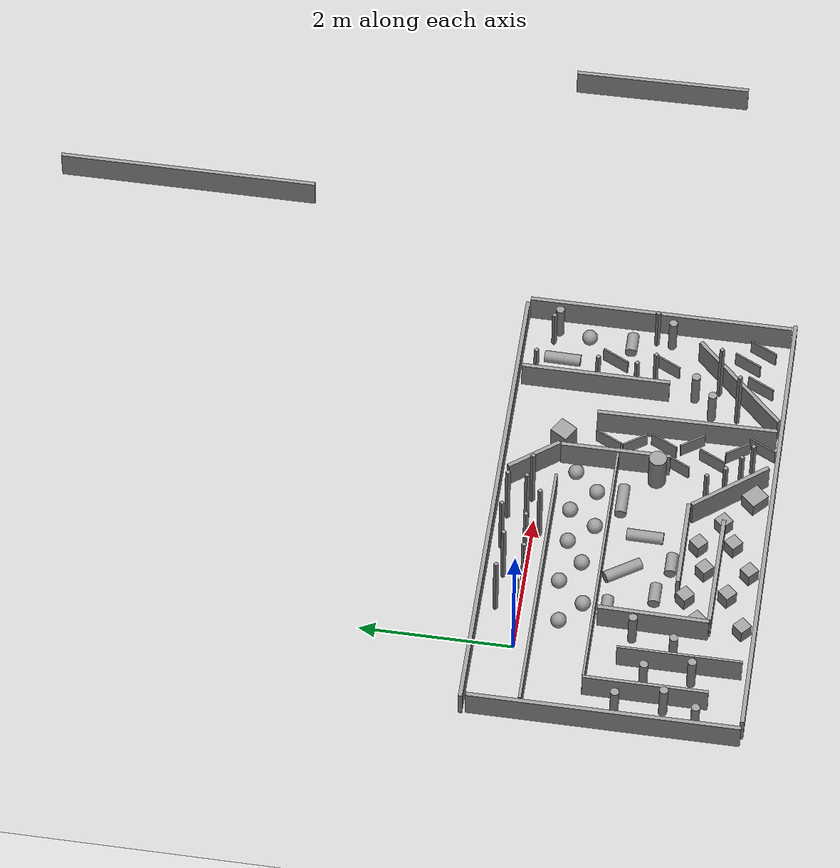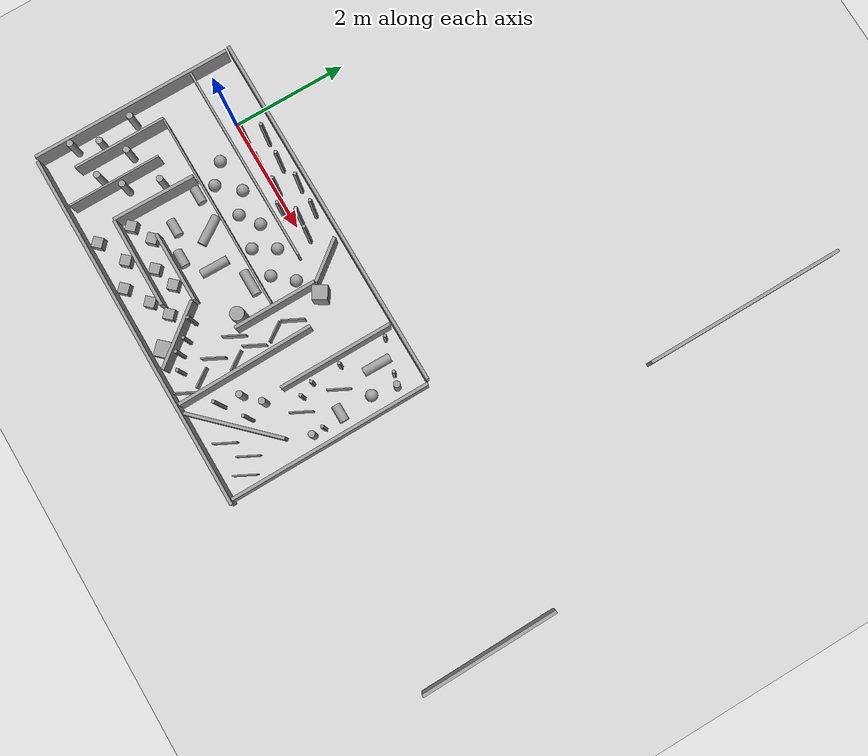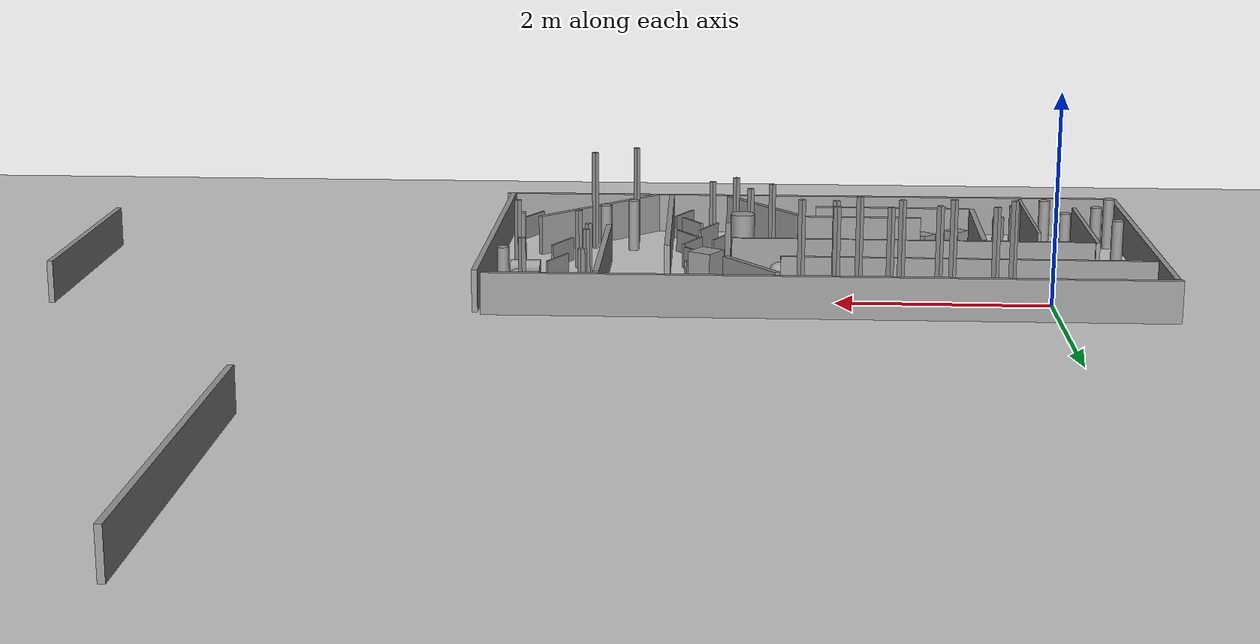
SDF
<sdf version="1.7">
 <world name="default">
  <light name="sun" type="directional">
   <pose>0 0 10 0 -0 0</pose>
   <diffuse>0.8 0.8 0.8 1</diffuse>
   <specular>0.2 0.2 0.2 1</specular>
   <attenuation>
    <range>1000</range>
    <constant>0.9</constant>
    <linear>0.01</linear>
    <quadratic>0.001</quadratic>
   </attenuation>
   <direction>-0.5 0.1 -0.9</direction>
   <spot><inner_angle>0</inner_angle><outer_angle>0</outer_angle><falloff>0</falloff></spot>
  </light>
  <model name="ground_plane">
   <static>1</static>
   <link name="link">
    <collision name="collision">
     <geometry><plane><normal>0 0 1</normal><size>100 100</size></plane></geometry>
     <surface>
      <contact><collide_bitmask>65535</collide_bitmask></contact>
      <friction><ode><mu>100</mu><mu2>50</mu2></ode></friction>
     </surface>
    </collision>
    <visual name="visual">
     <cast_shadows>0</cast_shadows>
     <geometry><plane><normal>0 0 1</normal><size>100 100</size></plane></geometry>
     <material>
      <script><uri>file://media/materials/scripts/gazebo.material</uri><name>Gazebo/Grey</name></script>
     </material>
    </visual>
   </link>
  </model>
  <gravity>0 0 -9.8</gravity>
  <magnetic_field>6e-06 2.3e-05 -4.2e-05</magnetic_field>
  <atmosphere type="adiabatic"/>
  <physics type="ode">
   <max_step_size>0.001</max_step_size>
   <real_time_factor>1</real_time_factor>
   <real_time_update_rate>1000</real_time_update_rate>
  </physics>
  <scene><ambient>0.4 0.4 0.4 1</ambient><background>0.7 0.7 0.7 1</background><shadows>1</shadows></scene>
  <spherical_coordinates>
   <surface_model>EARTH_WGS84</surface_model>
   <latitude_deg>0</latitude_deg>
   <longitude_deg>0</longitude_deg>
   <elevation>0</elevation>
   <heading_deg>0</heading_deg>
  </spherical_coordinates>
  <model name="unit_box">
   <pose>2.08568 0.530291 0.193139 0.002818 0.00144 0.000198</pose>
   <link name="link">
    <inertial>
     <mass>1</mass>
     <inertia>
      <ixx>0.166667</ixx>
      <ixy>0</ixy>
      <ixz>0</ixz>
      <iyy>0.166667</iyy>
      <iyz>0</iyz>
      <izz>0.166667</izz>
     </inertia>
    </inertial>
    <collision name="collision"><geometry><box><size>6.34126 0.053487 0.395256</size></box></geometry></collision>
    <visual name="visual">
     <geometry><box><size>6.34126 0.053487 0.395256</size></box></geometry>
     <material>
      <script><name>Gazebo/Grey</name><uri>file://media/materials/scripts/gazebo.material</uri></script>
     </material>
    </visual>
   </link>
  </model>
  <model name="unit_box_clone">
   <pose>2.21448 -3.04552 0.191305 0.00143 0.002007 -0.000165</pose>
   <link name="link">
    <inertial>
     <mass>1</mass>
     <inertia>
      <ixx>0.166667</ixx>
      <ixy>0</ixy>
      <ixz>0</ixz>
      <iyy>0.166667</iyy>
      <iyz>0</iyz>
      <izz>0.166667</izz>
     </inertia>
    </inertial>
    <collision name="collision"><geometry><box><size>6.34126 0.053487 0.395257</size></box></geometry></collision>
    <visual name="visual">
     <geometry><box><size>6.34126 0.053487 0.395257</size></box></geometry>
     <material>
      <script><name>Gazebo/Grey</name><uri>file://media/materials/scripts/gazebo.material</uri></script>
     </material>
    </visual>
   </link>
  </model>
  <model name="unit_box_clone_0">
   <pose>-1.04258 -1.28909 0.197473 0.00021 9.2e-05 -1.57068</pose>
   <link name="link">
    <inertial>
     <mass>1</mass>
     <inertia>
      <ixx>0.166667</ixx>
      <ixy>0</ixy>
      <ixz>0</ixz>
      <iyy>0.166667</iyy>
      <iyz>0</iyz>
      <izz>0.166667</izz>
     </inertia>
    </inertial>
    <collision name="collision"><geometry><box><size>3.50364 0.053487 0.395257</size></box></geometry></collision>
    <visual name="visual">
     <geometry><box><size>3.50364 0.053487 0.395257</size></box></geometry>
     <material>
      <script><name>Gazebo/Grey</name><uri>file://media/materials/scripts/gazebo.material</uri></script>
     </material>
    </visual>
   </link>
  </model>
  <model name="unit_box_clone_0_clone">
   <pose>5.31635 -1.2526 0.197473 0.00021 9.2e-05 -1.57074</pose>
   <link name="link">
    <inertial>
     <mass>1</mass>
     <inertia>
      <ixx>0.166667</ixx>
      <ixy>0</ixy>
      <ixz>0</ixz>
      <iyy>0.166667</iyy>
      <iyz>0</iyz>
      <izz>0.166667</izz>
     </inertia>
    </inertial>
    <collision name="collision"><geometry><box><size>3.50364 0.053487 0.395257</size></box></geometry></collision>
    <visual name="visual">
     <geometry><box><size>3.50364 0.053487 0.395257</size></box></geometry>
     <material>
      <script><name>Gazebo/Grey</name><uri>file://media/materials/scripts/gazebo.material</uri></script>
     </material>
    </visual>
   </link>
  </model>
  <light name="user_directional_light_0" type="directional">
   <pose>1.95604 -3.78033 1 0 -0 0</pose>
   <diffuse>0.5 0.5 0.5 1</diffuse>
   <specular>0.1 0.1 0.1 1</specular>
   <direction>0.1 0.1 -0.9</direction>
   <attenuation>
    <range>20</range>
    <constant>0.5</constant>
    <linear>0.01</linear>
    <quadratic>0.001</quadratic>
   </attenuation>
  </light>
  <light name="user_directional_light_1" type="directional">
   <pose>1.91014 0.829513 1 0 -0 0</pose>
   <diffuse>0.5 0.5 0.5 1</diffuse>
   <specular>0.1 0.1 0.1 1</specular>
   <direction>0.1 0.1 -0.9</direction>
   <attenuation>
    <range>20</range>
    <constant>0.5</constant>
    <linear>0.01</linear>
    <quadratic>0.001</quadratic>
   </attenuation>
  </light>
  <light name="user_point_light_0" type="point">
   <pose>4.8797 -0.024713 1 0 -0 0</pose>
   <diffuse>0.5 0.5 0.5 1</diffuse>
   <specular>0.1 0.1 0.1 1</specular>
   <attenuation>
    <range>20</range>
    <constant>0.5</constant>
    <linear>0.01</linear>
    <quadratic>0.001</quadratic>
   </attenuation>
   <cast_shadows>0</cast_shadows>
   <direction>0 0 -1</direction>
  </light>
  <light name="user_point_light_1" type="point">
   <pose>4.9247 -2.9283 1 0 -0 0</pose>
   <diffuse>0.5 0.5 0.5 1</diffuse>
   <specular>0.1 0.1 0.1 1</specular>
   <attenuation>
    <range>20</range>
    <constant>0.5</constant>
    <linear>0.01</linear>
    <quadratic>0.001</quadratic>
   </attenuation>
   <cast_shadows>0</cast_shadows>
   <direction>0 0 -1</direction>
  </light>
  <light name="user_point_light_2" type="point">
   <pose>-0.688319 -0.249503 1 0 -0 0</pose>
   <diffuse>0.5 0.5 0.5 1</diffuse>
   <specular>0.1 0.1 0.1 1</specular>
   <attenuation>
    <range>20</range>
    <constant>0.5</constant>
    <linear>0.01</linear>
    <quadratic>0.001</quadratic>
   </attenuation>
   <cast_shadows>0</cast_shadows>
   <direction>0 0 -1</direction>
  </light>
  <light name="user_point_light_3" type="point">
   <pose>-0.743445 -2.97262 1 0 -0 0</pose>
   <diffuse>0.5 0.5 0.5 1</diffuse>
   <specular>0.1 0.1 0.1 1</specular>
   <attenuation>
    <range>20</range>
    <constant>0.5</constant>
    <linear>0.01</linear>
    <quadratic>0.001</quadratic>
   </attenuation>
   <cast_shadows>0</cast_shadows>
   <direction>0 0 -1</direction>
  </light>
  <model name="unit_box_clone_0_clone_clone">
   <pose>3.6045 -1.80754 0.197525 -2e-06 -8.7e-05 -1.5579</pose>
   <link name="link">
    <inertial>
     <mass>1</mass>
     <inertia>
      <ixx>0.166667</ixx>
      <ixy>0</ixy>
      <ixz>0</ixz>
      <iyy>0.166667</iyy>
      <iyz>0</iyz>
      <izz>0.166667</izz>
     </inertia>
    </inertial>
    <collision name="collision"><geometry><box><size>2.37247 0.053487 0.395257</size></box></geometry></collision>
    <visual name="visual">
     <geometry><box><size>2.37247 0.053487 0.395257</size></box></geometry>
     <material>
      <script><name>Gazebo/Grey</name><uri>file://media/materials/scripts/gazebo.material</uri></script>
     </material>
    </visual>
   </link>
  </model>
  <model name="unit_box_clone_0_clone_clone_0">
   <pose>3.00883 -0.935932 0.197619 0 -1.3e-05 -1.56742</pose>
   <link name="link">
    <inertial>
     <mass>1</mass>
     <inertia>
      <ixx>0.166667</ixx>
      <ixy>0</ixy>
      <ixz>0</ixz>
      <iyy>0.166667</iyy>
      <iyz>0</iyz>
      <izz>0.166667</izz>
     </inertia>
    </inertial>
    <collision name="collision"><geometry><box><size>1.44105 0.053487 0.395257</size></box></geometry></collision>
    <visual name="visual">
     <geometry><box><size>1.44105 0.053487 0.395257</size></box></geometry>
     <material>
      <script><name>Gazebo/Grey</name><uri>file://media/materials/scripts/gazebo.material</uri></script>
     </material>
    </visual>
   </link>
  </model>
  <model name="unit_box_clone_0_clone_clone_1">
   <pose>2.78911 0.112179 0.197628 1e-06 -0 -0.912313</pose>
   <link name="link">
    <inertial>
     <mass>1</mass>
     <inertia>
      <ixx>0.166667</ixx>
      <ixy>0</ixy>
      <ixz>0</ixz>
      <iyy>0.166667</iyy>
      <iyz>0</iyz>
      <izz>0.166667</izz>
     </inertia>
    </inertial>
    <collision name="collision">
     <geometry><box><size>0.781865 0.053487 0.395257</size></box></geometry>
    </collision>
    <visual name="visual">
     <geometry><box><size>0.781865 0.053487 0.395257</size></box></geometry>
     <material>
      <script><name>Gazebo/Grey</name><uri>file://media/materials/scripts/gazebo.material</uri></script>
     </material>
    </visual>
   </link>
  </model>
  <model name="unit_box_clone_0_clone_clone_2">
   <pose>0.75471 -0.216927 0.197498 0.000136 7.6e-05 -3.14158</pose>
   <link name="link">
    <inertial>
     <mass>1</mass>
     <inertia>
      <ixx>0.166667</ixx>
      <ixy>0</ixy>
      <ixz>0</ixz>
      <iyy>0.166667</iyy>
      <iyz>0</iyz>
      <izz>0.166667</izz>
     </inertia>
    </inertial>
    <collision name="collision">
     <geometry><box><size>3.50364 0.0374877 0.395257</size></box></geometry>
    </collision>
    <visual name="visual">
     <geometry><box><size>3.50364 0.0374877 0.395257</size></box></geometry>
     <material>
      <script><name>Gazebo/Grey</name><uri>file://media/materials/scripts/gazebo.material</uri></script>
     </material>
    </visual>
   </link>
  </model>
  <model name="unit_box_clone_0_clone_clone_3">
   <pose>6.81856 5.42163 0.197473 0.00021 -9.2e-05 -1.571</pose>
   <link name="link">
    <inertial>
     <mass>1</mass>
     <inertia>
      <ixx>0.166667</ixx>
      <ixy>0</ixy>
      <ixz>0</ixz>
      <iyy>0.166667</iyy>
      <iyz>0</iyz>
      <izz>0.166667</izz>
     </inertia>
    </inertial>
    <collision name="collision"><geometry><box><size>3.50364 0.053487 0.395257</size></box></geometry></collision>
    <visual name="visual">
     <geometry><box><size>3.50364 0.053487 0.395257</size></box></geometry>
     <material>
      <script><name>Gazebo/Grey</name><uri>file://media/materials/scripts/gazebo.material</uri></script>
     </material>
    </visual>
   </link>
  </model>
  <model name="unit_box_clone_0_clone_clone_clone">
   <pose>4.34729 -2.41444 0.197611 -1e-06 -2.1e-05 -2.35173</pose>
   <link name="link">
    <inertial>
     <mass>1</mass>
     <inertia>
      <ixx>0.166667</ixx>
      <ixy>0</ixy>
      <ixz>0</ixz>
      <iyy>0.166667</iyy>
      <iyz>0</iyz>
      <izz>0.166667</izz>
     </inertia>
    </inertial>
    <collision name="collision"><geometry><box><size>1.63225 0.053487 0.395257</size></box></geometry></collision>
    <visual name="visual">
     <geometry><box><size>1.63225 0.053487 0.395257</size></box></geometry>
     <material>
      <script><name>Gazebo/Grey</name><uri>file://media/materials/scripts/gazebo.material</uri></script>
     </material>
    </visual>
   </link>
  </model>
  <model name="unit_box_clone_0_clone_clone_clone_1">
   <pose>-0.561989 -1.76641 0.197612 0 -2e-05 -1.57222</pose>
   <link name="link">
    <inertial>
     <mass>1</mass>
     <inertia>
      <ixx>0.166667</ixx>
      <ixy>0</ixy>
      <ixz>0</ixz>
      <iyy>0.166667</iyy>
      <iyz>0</iyz>
      <izz>0.166667</izz>
     </inertia>
    </inertial>
    <collision name="collision">
     <geometry><box><size>1.61173 0.0400308 0.395257</size></box></geometry>
    </collision>
    <visual name="visual">
     <geometry><box><size>1.61173 0.0400308 0.395257</size></box></geometry>
     <material>
      <script><name>Gazebo/Grey</name><uri>file://media/materials/scripts/gazebo.material</uri></script>
     </material>
    </visual>
   </link>
  </model>
  <model name="unit_box_clone_0_clone_clone_2_clone_0">
   <pose>1.31791 -2.45785 0.197614 -1e-06 -1.8e-05 3.13434</pose>
   <link name="link">
    <inertial>
     <mass>1</mass>
     <inertia>
      <ixx>0.166667</ixx>
      <ixy>0</ixy>
      <ixz>0</ixz>
      <iyy>0.166667</iyy>
      <iyz>0</iyz>
      <izz>0.166667</izz>
     </inertia>
    </inertial>
    <collision name="collision"><geometry><box><size>1.57414 0.053487 0.395257</size></box></geometry></collision>
    <visual name="visual">
     <geometry><box><size>1.57414 0.053487 0.395257</size></box></geometry>
     <material>
      <script><name>Gazebo/Grey</name><uri>file://media/materials/scripts/gazebo.material</uri></script>
     </material>
    </visual>
   </link>
  </model>
  <model name="unit_box_clone_0_clone_clone_2_clone_1">
   <pose>1.21627 -0.969887 0.197105 9e-05 0.0003 3.14155</pose>
   <link name="link">
    <inertial>
     <mass>1</mass>
     <inertia>
      <ixx>0.166667</ixx>
      <ixy>0</ixy>
      <ixz>0</ixz>
      <iyy>0.166667</iyy>
      <iyz>0</iyz>
      <izz>0.166667</izz>
     </inertia>
    </inertial>
    <collision name="collision">
     <geometry><box><size>3.50364 0.0305089 0.395257</size></box></geometry>
    </collision>
    <visual name="visual">
     <geometry><box><size>3.50364 0.0305089 0.395257</size></box></geometry>
     <material>
      <script><name>Gazebo/Grey</name><uri>file://media/materials/scripts/gazebo.material</uri></script>
     </material>
    </visual>
   </link>
  </model>
  <model name="unit_box_clone_0_clone_clone_clone_1_clone_1">
   <pose>-0.049894 -2.14178 0.197612 0 2e-05 -1.57115</pose>
   <link name="link">
    <inertial>
     <mass>1</mass>
     <inertia>
      <ixx>0.166667</ixx>
      <ixy>0</ixy>
      <ixz>0</ixz>
      <iyy>0.166667</iyy>
      <iyz>0</iyz>
      <izz>0.166667</izz>
     </inertia>
    </inertial>
    <collision name="collision">
     <geometry><box><size>1.61173 0.0303199 0.395257</size></box></geometry>
    </collision>
    <visual name="visual">
     <geometry><box><size>1.61173 0.0303199 0.395257</size></box></geometry>
     <material>
      <script><name>Gazebo/Grey</name><uri>file://media/materials/scripts/gazebo.material</uri></script>
     </material>
    </visual>
   </link>
  </model>
  <model name="unit_box_clone_0_clone_clone_clone_1_clone_4">
   <pose>0.514522 -1.73573 0.19762 0 -1.3e-05 -1.58624</pose>
   <link name="link">
    <inertial>
     <mass>1</mass>
     <inertia>
      <ixx>0.166667</ixx>
      <ixy>0</ixy>
      <ixz>0</ixz>
      <iyy>0.166667</iyy>
      <iyz>0</iyz>
      <izz>0.166667</izz>
     </inertia>
    </inertial>
    <collision name="collision"><geometry><box><size>1.43724 0.053487 0.395257</size></box></geometry></collision>
    <visual name="visual">
     <geometry><box><size>1.43724 0.053487 0.395257</size></box></geometry>
     <material>
      <script><name>Gazebo/Grey</name><uri>file://media/materials/scripts/gazebo.material</uri></script>
     </material>
    </visual>
   </link>
  </model>
  <model name="unit_box_clone_0_clone_clone_2_clone_0_clone">
   <pose>2.64848 -2.48151 0.200292 0 9e-06 2.23807</pose>
   <link name="link">
    <inertial>
     <mass>1</mass>
     <inertia>
      <ixx>0.166667</ixx>
      <ixy>0</ixy>
      <ixz>0</ixz>
      <iyy>0.166667</iyy>
      <iyz>0</iyz>
      <izz>0.166667</izz>
     </inertia>
    </inertial>
    <collision name="collision"><geometry><box><size>1.17612 0.053487 0.400593</size></box></geometry></collision>
    <visual name="visual">
     <geometry><box><size>1.17612 0.053487 0.400593</size></box></geometry>
     <material>
      <script><name>Gazebo/Grey</name><uri>file://media/materials/scripts/gazebo.material</uri></script>
     </material>
    </visual>
   </link>
  </model>
  <model name="unit_box_clone_0_clone_clone_2_clone_0_clone_0">
   <pose>1.67874 -1.98332 0.197624 -0 -8e-06 -3.1407</pose>
   <link name="link">
    <inertial>
     <mass>1</mass>
     <inertia>
      <ixx>0.166667</ixx>
      <ixy>0</ixy>
      <ixz>0</ixz>
      <iyy>0.166667</iyy>
      <iyz>0</iyz>
      <izz>0.166667</izz>
     </inertia>
    </inertial>
    <collision name="collision"><geometry><box><size>1.23261 0.053487 0.395257</size></box></geometry></collision>
    <visual name="visual">
     <geometry><box><size>1.23261 0.053487 0.395257</size></box></geometry>
     <material>
      <script><name>Gazebo/Grey</name><uri>file://media/materials/scripts/gazebo.material</uri></script>
     </material>
    </visual>
   </link>
  </model>
  <model name="unit_box_1">
   <pose>3.20971 -0.223291 0.218642 0 -0 1.01757</pose>
   <link name="link">
    <inertial>
     <mass>1</mass>
     <inertia>
      <ixx>0.166667</ixx>
      <ixy>0</ixy>
      <ixz>0</ixz>
      <iyy>0.166667</iyy>
      <iyz>0</iyz>
      <izz>0.166667</izz>
     </inertia>
    </inertial>
    <collision name="collision">
     <geometry><box><size>0.249472 0.238991 0.437285</size></box></geometry>
    </collision>
    <visual name="visual">
     <geometry><box><size>0.249472 0.238991 0.437285</size></box></geometry>
     <material>
      <script><name>Gazebo/Grey</name><uri>file://media/materials/scripts/gazebo.material</uri></script>
     </material>
    </visual>
   </link>
  </model>
  <model name="unit_box_clone_0_clone_clone_2_clone_2">
   <pose>4.20162 -0.517801 0.197586 1e-06 4.3e-05 1.56996</pose>
   <link name="link">
    <inertial>
     <mass>1</mass>
     <inertia>
      <ixx>0.166667</ixx>
      <ixy>0</ixy>
      <ixz>0</ixz>
      <iyy>0.166667</iyy>
      <iyz>0</iyz>
      <izz>0.166667</izz>
     </inertia>
    </inertial>
    <collision name="collision"><geometry><box><size>1.96899 0.053487 0.395257</size></box></geometry></collision>
    <visual name="visual">
     <geometry><box><size>1.96899 0.053487 0.395257</size></box></geometry>
     <material>
      <script><name>Gazebo/Grey</name><uri>file://media/materials/scripts/gazebo.material</uri></script>
     </material>
    </visual>
   </link>
  </model>
  <model name="unit_box_2_clone_0">
   <pose>0.376658 0.020895 0.5 1e-06 2e-06 -0.765532</pose>
   <link name="link">
    <inertial>
     <mass>1</mass>
     <inertia>
      <ixx>0.166667</ixx>
      <ixy>0</ixy>
      <ixz>0</ixz>
      <iyy>0.166667</iyy>
      <iyz>0</iyz>
      <izz>0.166667</izz>
     </inertia>
    </inertial>
    <collision name="collision"><geometry><box><size>0.0488997 0.0476357 1</size></box></geometry></collision>
    <visual name="visual">
     <geometry><box><size>0.0488997 0.0476357 1</size></box></geometry>
     <material>
      <script><name>Gazebo/Grey</name><uri>file://media/materials/scripts/gazebo.material</uri></script>
     </material>
    </visual>
   </link>
  </model>
  <model name="unit_sphere_clone_2">
   <pose>0.433808 -0.529917 0.103079 0 -0 0</pose>
   <link name="link">
    <inertial>
     <mass>1</mass>
     <inertia><ixx>0.1</ixx><ixy>0</ixy><ixz>0</ixz><iyy>0.1</iyy><iyz>0</iyz><izz>0.1</izz></inertia>
    </inertial>
    <collision name="collision"><geometry><sphere><radius>0.103079</radius></sphere></geometry></collision>
    <visual name="visual">
     <geometry><sphere><radius>0.103079</radius></sphere></geometry>
     <material>
      <script><name>Gazebo/Grey</name><uri>file://media/materials/scripts/gazebo.material</uri></script>
     </material>
    </visual>
   </link>
  </model>
  <model name="unit_sphere_clone_2_clone">
   <pose>2.78446 -0.450412 0.103079 0 -0 0</pose>
   <link name="link">
    <inertial>
     <mass>1</mass>
     <inertia><ixx>0.1</ixx><ixy>0</ixy><ixz>0</ixz><iyy>0.1</iyy><iyz>0</iyz><izz>0.1</izz></inertia>
    </inertial>
    <collision name="collision"><geometry><sphere><radius>0.103079</radius></sphere></geometry></collision>
    <visual name="visual">
     <geometry><sphere><radius>0.103079</radius></sphere></geometry>
     <material>
      <script><name>Gazebo/Grey</name><uri>file://media/materials/scripts/gazebo.material</uri></script>
     </material>
    </visual>
   </link>
  </model>
  <model name="unit_sphere_clone_2_clone_0">
   <pose>2.50719 -0.761141 0.103079 0 -0 0</pose>
   <link name="link">
    <inertial>
     <mass>1</mass>
     <inertia><ixx>0.1</ixx><ixy>0</ixy><ixz>0</ixz><iyy>0.1</iyy><iyz>0</iyz><izz>0.1</izz></inertia>
    </inertial>
    <collision name="collision"><geometry><sphere><radius>0.103079</radius></sphere></geometry></collision>
    <visual name="visual">
     <geometry><sphere><radius>0.103079</radius></sphere></geometry>
     <material>
      <script><name>Gazebo/Grey</name><uri>file://media/materials/scripts/gazebo.material</uri></script>
     </material>
    </visual>
   </link>
  </model>
  <model name="unit_sphere_clone_2_clone_1">
   <pose>2.17445 -0.449568 0.103079 0 -0 0</pose>
   <link name="link">
    <inertial>
     <mass>1</mass>
     <inertia><ixx>0.1</ixx><ixy>0</ixy><ixz>0</ixz><iyy>0.1</iyy><iyz>0</iyz><izz>0.1</izz></inertia>
    </inertial>
    <collision name="collision"><geometry><sphere><radius>0.103079</radius></sphere></geometry></collision>
    <visual name="visual">
     <geometry><sphere><radius>0.103079</radius></sphere></geometry>
     <material>
      <script><name>Gazebo/Grey</name><uri>file://media/materials/scripts/gazebo.material</uri></script>
     </material>
    </visual>
   </link>
  </model>
  <model name="unit_sphere_clone_2_clone_2">
   <pose>1.96376 -0.802286 0.103079 0 -0 0</pose>
   <link name="link">
    <inertial>
     <mass>1</mass>
     <inertia><ixx>0.1</ixx><ixy>0</ixy><ixz>0</ixz><iyy>0.1</iyy><iyz>0</iyz><izz>0.1</izz></inertia>
    </inertial>
    <collision name="collision"><geometry><sphere><radius>0.103079</radius></sphere></geometry></collision>
    <visual name="visual">
     <geometry><sphere><radius>0.103079</radius></sphere></geometry>
     <material>
      <script><name>Gazebo/Grey</name><uri>file://media/materials/scripts/gazebo.material</uri></script>
     </material>
    </visual>
   </link>
  </model>
  <model name="unit_sphere_clone_2_clone_3">
   <pose>1.37012 -0.706616 0.103079 0 -0 0</pose>
   <link name="link">
    <inertial>
     <mass>1</mass>
     <inertia><ixx>0.1</ixx><ixy>0</ixy><ixz>0</ixz><iyy>0.1</iyy><iyz>0</iyz><izz>0.1</izz></inertia>
    </inertial>
    <collision name="collision"><geometry><sphere><radius>0.103079</radius></sphere></geometry></collision>
    <visual name="visual">
     <geometry><sphere><radius>0.103079</radius></sphere></geometry>
     <material>
      <script><name>Gazebo/Grey</name><uri>file://media/materials/scripts/gazebo.material</uri></script>
     </material>
    </visual>
   </link>
  </model>
  <model name="unit_sphere_clone_2_clone_4">
   <pose>1.68186 -0.484583 0.103079 0 -0 0</pose>
   <link name="link">
    <inertial>
     <mass>1</mass>
     <inertia><ixx>0.1</ixx><ixy>0</ixy><ixz>0</ixz><iyy>0.1</iyy><iyz>0</iyz><izz>0.1</izz></inertia>
    </inertial>
    <collision name="collision"><geometry><sphere><radius>0.103079</radius></sphere></geometry></collision>
    <visual name="visual">
     <geometry><sphere><radius>0.103079</radius></sphere></geometry>
     <material>
      <script><name>Gazebo/Grey</name><uri>file://media/materials/scripts/gazebo.material</uri></script>
     </material>
    </visual>
   </link>
  </model>
  <model name="unit_sphere_clone_2_clone_5">
   <pose>1.04544 -0.45494 0.103079 0 -0 0</pose>
   <link name="link">
    <inertial>
     <mass>1</mass>
     <inertia><ixx>0.1</ixx><ixy>0</ixy><ixz>0</ixz><iyy>0.1</iyy><iyz>0</iyz><izz>0.1</izz></inertia>
    </inertial>
    <collision name="collision"><geometry><sphere><radius>0.103079</radius></sphere></geometry></collision>
    <visual name="visual">
     <geometry><sphere><radius>0.103079</radius></sphere></geometry>
     <material>
      <script><name>Gazebo/Grey</name><uri>file://media/materials/scripts/gazebo.material</uri></script>
     </material>
    </visual>
   </link>
  </model>
  <model name="unit_sphere_clone_2_clone_6">
   <pose>0.739935 -0.804241 0.103079 0 -0 0</pose>
   <link name="link">
    <inertial>
     <mass>1</mass>
     <inertia><ixx>0.1</ixx><ixy>0</ixy><ixz>0</ixz><iyy>0.1</iyy><iyz>0</iyz><izz>0.1</izz></inertia>
    </inertial>
    <collision name="collision"><geometry><sphere><radius>0.103079</radius></sphere></geometry></collision>
    <visual name="visual">
     <geometry><sphere><radius>0.103079</radius></sphere></geometry>
     <material>
      <script><name>Gazebo/Grey</name><uri>file://media/materials/scripts/gazebo.material</uri></script>
     </material>
    </visual>
   </link>
  </model>
  <model name="unit_box_2_clone_0_clone">
   <pose>2.01593 0.35727 0.500001 4.8e-05 -3e-06 -0.766421</pose>
   <link name="link">
    <inertial>
     <mass>1</mass>
     <inertia>
      <ixx>0.166667</ixx>
      <ixy>0</ixy>
      <ixz>0</ixz>
      <iyy>0.166667</iyy>
      <iyz>0</iyz>
      <izz>0.166667</izz>
     </inertia>
    </inertial>
    <collision name="collision"><geometry><box><size>0.0489 0.047636 1</size></box></geometry></collision>
    <visual name="visual">
     <geometry><box><size>0.0489 0.047636 1</size></box></geometry>
     <material>
      <script><name>Gazebo/Grey</name><uri>file://media/materials/scripts/gazebo.material</uri></script>
     </material>
    </visual>
   </link>
  </model>
  <model name="unit_box_2_clone_0_clone_0">
   <pose>1.52949 0.368409 0.500002 1.5e-05 -6.8e-05 -0.76604</pose>
   <link name="link">
    <inertial>
     <mass>1</mass>
     <inertia>
      <ixx>0.166667</ixx>
      <ixy>0</ixy>
      <ixz>0</ixz>
      <iyy>0.166667</iyy>
      <iyz>0</iyz>
      <izz>0.166667</izz>
     </inertia>
    </inertial>
    <collision name="collision"><geometry><box><size>0.0489 0.047636 1</size></box></geometry></collision>
    <visual name="visual">
     <geometry><box><size>0.0489 0.047636 1</size></box></geometry>
     <material>
      <script><name>Gazebo/Grey</name><uri>file://media/materials/scripts/gazebo.material</uri></script>
     </material>
    </visual>
   </link>
  </model>
  <model name="unit_box_2_clone_0_clone_1">
   <pose>1.785 -0.093979 0.5 -4e-06 -1e-06 -0.765354</pose>
   <link name="link">
    <inertial>
     <mass>1</mass>
     <inertia>
      <ixx>0.166667</ixx>
      <ixy>0</ixy>
      <ixz>0</ixz>
      <iyy>0.166667</iyy>
      <iyz>0</iyz>
      <izz>0.166667</izz>
     </inertia>
    </inertial>
    <collision name="collision"><geometry><box><size>0.0489 0.047636 1</size></box></geometry></collision>
    <visual name="visual">
     <geometry><box><size>0.0489 0.047636 1</size></box></geometry>
     <material>
      <script><name>Gazebo/Grey</name><uri>file://media/materials/scripts/gazebo.material</uri></script>
     </material>
    </visual>
   </link>
  </model>
  <model name="unit_box_2_clone_0_clone_2">
   <pose>2.32725 0.071071 0.5 -2e-06 -4e-06 -0.767231</pose>
   <link name="link">
    <inertial>
     <mass>1</mass>
     <inertia>
      <ixx>0.166667</ixx>
      <ixy>0</ixy>
      <ixz>0</ixz>
      <iyy>0.166667</iyy>
      <iyz>0</iyz>
      <izz>0.166667</izz>
     </inertia>
    </inertial>
    <collision name="collision"><geometry><box><size>0.0489 0.047636 1</size></box></geometry></collision>
    <visual name="visual">
     <geometry><box><size>0.0489 0.047636 1</size></box></geometry>
     <material>
      <script><name>Gazebo/Grey</name><uri>file://media/materials/scripts/gazebo.material</uri></script>
     </material>
    </visual>
   </link>
  </model>
  <model name="unit_box_2_clone_0_clone_3">
   <pose>0.926373 -0.003016 0.5 -2e-06 0 -0.767017</pose>
   <link name="link">
    <inertial>
     <mass>1</mass>
     <inertia>
      <ixx>0.166667</ixx>
      <ixy>0</ixy>
      <ixz>0</ixz>
      <iyy>0.166667</iyy>
      <iyz>0</iyz>
      <izz>0.166667</izz>
     </inertia>
    </inertial>
    <collision name="collision"><geometry><box><size>0.0489 0.047636 1</size></box></geometry></collision>
    <visual name="visual">
     <geometry><box><size>0.0489 0.047636 1</size></box></geometry>
     <material>
      <script><name>Gazebo/Grey</name><uri>file://media/materials/scripts/gazebo.material</uri></script>
     </material>
    </visual>
   </link>
  </model>
  <model name="unit_box_2_clone_0_clone_4">
   <pose>2.01093 0.105307 0.5 -1e-05 -8e-06 -0.765735</pose>
   <link name="link">
    <inertial>
     <mass>1</mass>
     <inertia>
      <ixx>0.166667</ixx>
      <ixy>0</ixy>
      <ixz>0</ixz>
      <iyy>0.166667</iyy>
      <iyz>0</iyz>
      <izz>0.166667</izz>
     </inertia>
    </inertial>
    <collision name="collision"><geometry><box><size>0.0489 0.047636 1</size></box></geometry></collision>
    <visual name="visual">
     <geometry><box><size>0.0489 0.047636 1</size></box></geometry>
     <material>
      <script><name>Gazebo/Grey</name><uri>file://media/materials/scripts/gazebo.material</uri></script>
     </material>
    </visual>
   </link>
  </model>
  <model name="unit_box_2_clone_0_clone_5">
   <pose>1.07884 0.280252 0.5 1e-06 -3e-06 -0.765343</pose>
   <link name="link">
    <inertial>
     <mass>1</mass>
     <inertia>
      <ixx>0.166667</ixx>
      <ixy>0</ixy>
      <ixz>0</ixz>
      <iyy>0.166667</iyy>
      <iyz>0</iyz>
      <izz>0.166667</izz>
     </inertia>
    </inertial>
    <collision name="collision"><geometry><box><size>0.0489 0.047636 1</size></box></geometry></collision>
    <visual name="visual">
     <geometry><box><size>0.0489 0.047636 1</size></box></geometry>
     <material>
      <script><name>Gazebo/Grey</name><uri>file://media/materials/scripts/gazebo.material</uri></script>
     </material>
    </visual>
   </link>
  </model>
  <model name="unit_box_2_clone_0_clone_6">
   <pose>1.40332 0.037556 0.500001 -1e-06 -2e-05 -0.766805</pose>
   <link name="link">
    <inertial>
     <mass>1</mass>
     <inertia>
      <ixx>0.166667</ixx>
      <ixy>0</ixy>
      <ixz>0</ixz>
      <iyy>0.166667</iyy>
      <iyz>0</iyz>
      <izz>0.166667</izz>
     </inertia>
    </inertial>
    <collision name="collision"><geometry><box><size>0.0489 0.047636 1</size></box></geometry></collision>
    <visual name="visual">
     <geometry><box><size>0.0489 0.047636 1</size></box></geometry>
     <material>
      <script><name>Gazebo/Grey</name><uri>file://media/materials/scripts/gazebo.material</uri></script>
     </material>
    </visual>
   </link>
  </model>
  <model name="unit_box_2_clone_0_clone_7">
   <pose>0.570801 0.308569 0.5 2e-06 6e-06 -0.766113</pose>
   <link name="link">
    <inertial>
     <mass>1</mass>
     <inertia>
      <ixx>0.166667</ixx>
      <ixy>0</ixy>
      <ixz>0</ixz>
      <iyy>0.166667</iyy>
      <iyz>0</iyz>
      <izz>0.166667</izz>
     </inertia>
    </inertial>
    <collision name="collision"><geometry><box><size>0.0489 0.047636 1</size></box></geometry></collision>
    <visual name="visual">
     <geometry><box><size>0.0489 0.047636 1</size></box></geometry>
     <material>
      <script><name>Gazebo/Grey</name><uri>file://media/materials/scripts/gazebo.material</uri></script>
     </material>
    </visual>
   </link>
  </model>
  <model name="unit_cylinder">
   <pose>0.340744 -1.49297 0.259329 0 -0 0.000534</pose>
   <link name="link">
    <inertial>
     <mass>1</mass>
     <inertia><ixx>0.145833</ixx><ixy>0</ixy><ixz>0</ixz><iyy>0.145833</iyy><iyz>0</iyz><izz>0.125</izz></inertia>
    </inertial>
    <collision name="collision">
     <geometry><cylinder><radius>0.0555864</radius><length>0.518668</length></cylinder></geometry>
    </collision>
    <visual name="visual">
     <geometry><cylinder><radius>0.0555864</radius><length>0.518668</length></cylinder></geometry>
     <material>
      <script><name>Gazebo/Grey</name><uri>file://media/materials/scripts/gazebo.material</uri></script>
     </material>
    </visual>
   </link>
  </model>
  <model name="unit_cylinder_clone">
   <pose>0.108292 -2.04494 0.259329 0 -0 0.00127</pose>
   <link name="link">
    <inertial>
     <mass>1</mass>
     <inertia><ixx>0.145833</ixx><ixy>0</ixy><ixz>0</ixz><iyy>0.145833</iyy><iyz>0</iyz><izz>0.125</izz></inertia>
    </inertial>
    <collision name="collision">
     <geometry><cylinder><radius>0.0555866</radius><length>0.518668</length></cylinder></geometry>
    </collision>
    <visual name="visual">
     <geometry><cylinder><radius>0.0555866</radius><length>0.518668</length></cylinder></geometry>
     <material>
      <script><name>Gazebo/Grey</name><uri>file://media/materials/scripts/gazebo.material</uri></script>
     </material>
    </visual>
   </link>
  </model>
  <model name="unit_cylinder_clone_0">
   <pose>-0.224355 -2.31907 0.259329 0 -0 0.001417</pose>
   <link name="link">
    <inertial>
     <mass>1</mass>
     <inertia><ixx>0.145833</ixx><ixy>0</ixy><ixz>0</ixz><iyy>0.145833</iyy><iyz>0</iyz><izz>0.125</izz></inertia>
    </inertial>
    <collision name="collision">
     <geometry><cylinder><radius>0.0555866</radius><length>0.518668</length></cylinder></geometry>
    </collision>
    <visual name="visual">
     <geometry><cylinder><radius>0.0555866</radius><length>0.518668</length></cylinder></geometry>
     <material>
      <script><name>Gazebo/Grey</name><uri>file://media/materials/scripts/gazebo.material</uri></script>
     </material>
    </visual>
   </link>
  </model>
  <model name="unit_cylinder_clone_1">
   <pose>-0.898649 -2.44344 0.259329 0 -0 0.00046</pose>
   <link name="link">
    <inertial>
     <mass>1</mass>
     <inertia><ixx>0.145833</ixx><ixy>0</ixy><ixz>0</ixz><iyy>0.145833</iyy><iyz>0</iyz><izz>0.125</izz></inertia>
    </inertial>
    <collision name="collision">
     <geometry><cylinder><radius>0.0555866</radius><length>0.518668</length></cylinder></geometry>
    </collision>
    <visual name="visual">
     <geometry><cylinder><radius>0.0555866</radius><length>0.518668</length></cylinder></geometry>
     <material>
      <script><name>Gazebo/Grey</name><uri>file://media/materials/scripts/gazebo.material</uri></script>
     </material>
    </visual>
   </link>
  </model>
  <model name="unit_cylinder_clone_2">
   <pose>-0.815607 -1.40514 0.259329 0 -0 0.001749</pose>
   <link name="link">
    <inertial>
     <mass>1</mass>
     <inertia><ixx>0.145833</ixx><ixy>0</ixy><ixz>0</ixz><iyy>0.145833</iyy><iyz>0</iyz><izz>0.125</izz></inertia>
    </inertial>
    <collision name="collision">
     <geometry><cylinder><radius>0.0555866</radius><length>0.518668</length></cylinder></geometry>
    </collision>
    <visual name="visual">
     <geometry><cylinder><radius>0.0555866</radius><length>0.518668</length></cylinder></geometry>
     <material>
      <script><name>Gazebo/Grey</name><uri>file://media/materials/scripts/gazebo.material</uri></script>
     </material>
    </visual>
   </link>
  </model>
  <model name="unit_cylinder_clone_3">
   <pose>-0.701435 -2.01697 0.259329 0 -0 0.000493</pose>
   <link name="link">
    <inertial>
     <mass>1</mass>
     <inertia><ixx>0.145833</ixx><ixy>0</ixy><ixz>0</ixz><iyy>0.145833</iyy><iyz>0</iyz><izz>0.125</izz></inertia>
    </inertial>
    <collision name="collision">
     <geometry><cylinder><radius>0.0555866</radius><length>0.518668</length></cylinder></geometry>
    </collision>
    <visual name="visual">
     <geometry><cylinder><radius>0.0555866</radius><length>0.518668</length></cylinder></geometry>
     <material>
      <script><name>Gazebo/Grey</name><uri>file://media/materials/scripts/gazebo.material</uri></script>
     </material>
    </visual>
   </link>
  </model>
  <model name="unit_cylinder_clone_4">
   <pose>-0.346794 -1.71643 0.259329 0 -0 0.000649</pose>
   <link name="link">
    <inertial>
     <mass>1</mass>
     <inertia><ixx>0.145833</ixx><ixy>0</ixy><ixz>0</ixz><iyy>0.145833</iyy><iyz>0</iyz><izz>0.125</izz></inertia>
    </inertial>
    <collision name="collision">
     <geometry><cylinder><radius>0.0555866</radius><length>0.518668</length></cylinder></geometry>
    </collision>
    <visual name="visual">
     <geometry><cylinder><radius>0.0555866</radius><length>0.518668</length></cylinder></geometry>
     <material>
      <script><name>Gazebo/Grey</name><uri>file://media/materials/scripts/gazebo.material</uri></script>
     </material>
    </visual>
   </link>
  </model>
  <model name="unit_box_0">
   <pose>0.632123 -2.87479 0.101363 -2e-06 -4e-06 0.821388</pose>
   <link name="link">
    <inertial>
     <mass>1</mass>
     <inertia>
      <ixx>0.166667</ixx>
      <ixy>0</ixy>
      <ixz>0</ixz>
      <iyy>0.166667</iyy>
      <iyz>0</iyz>
      <izz>0.166667</izz>
     </inertia>
    </inertial>
    <collision name="collision">
     <geometry><box><size>0.171909 0.173277 0.202726</size></box></geometry>
    </collision>
    <visual name="visual">
     <geometry><box><size>0.171909 0.173277 0.202726</size></box></geometry>
     <material>
      <script><name>Gazebo/Grey</name><uri>file://media/materials/scripts/gazebo.material</uri></script>
     </material>
    </visual>
   </link>
  </model>
  <model name="unit_box_0_clone">
   <pose>1.50737 -2.87209 0.101362 -1e-06 5e-06 0.821358</pose>
   <link name="link">
    <inertial>
     <mass>1</mass>
     <inertia>
      <ixx>0.166667</ixx>
      <ixy>0</ixy>
      <ixz>0</ixz>
      <iyy>0.166667</iyy>
      <iyz>0</iyz>
      <izz>0.166667</izz>
     </inertia>
    </inertial>
    <collision name="collision">
     <geometry><box><size>0.171909 0.173277 0.202726</size></box></geometry>
    </collision>
    <visual name="visual">
     <geometry><box><size>0.171909 0.173277 0.202726</size></box></geometry>
     <material>
      <script><name>Gazebo/Grey</name><uri>file://media/materials/scripts/gazebo.material</uri></script>
     </material>
    </visual>
   </link>
  </model>
  <model name="unit_box_0_clone_0">
   <pose>2.23693 -2.45505 0.101363 -2e-06 -4e-06 0.821372</pose>
   <link name="link">
    <inertial>
     <mass>1</mass>
     <inertia>
      <ixx>0.166667</ixx>
      <ixy>0</ixy>
      <ixz>0</ixz>
      <iyy>0.166667</iyy>
      <iyz>0</iyz>
      <izz>0.166667</izz>
     </inertia>
    </inertial>
    <collision name="collision">
     <geometry><box><size>0.171909 0.173277 0.202726</size></box></geometry>
    </collision>
    <visual name="visual">
     <geometry><box><size>0.171909 0.173277 0.202726</size></box></geometry>
     <material>
      <script><name>Gazebo/Grey</name><uri>file://media/materials/scripts/gazebo.material</uri></script>
     </material>
    </visual>
   </link>
  </model>
  <model name="unit_box_0_clone_1">
   <pose>2.67652 -2.81492 0.101363 0 -0 0.821416</pose>
   <link name="link">
    <inertial>
     <mass>1</mass>
     <inertia>
      <ixx>0.166667</ixx>
      <ixy>0</ixy>
      <ixz>0</ixz>
      <iyy>0.166667</iyy>
      <iyz>0</iyz>
      <izz>0.166667</izz>
     </inertia>
    </inertial>
    <collision name="collision"><geometry><box><size>0.23422 0.263927 0.202726</size></box></geometry></collision>
    <visual name="visual">
     <geometry><box><size>0.23422 0.263927 0.202726</size></box></geometry>
     <material>
      <script><name>Gazebo/Grey</name><uri>file://media/materials/scripts/gazebo.material</uri></script>
     </material>
    </visual>
   </link>
  </model>
  <model name="unit_box_0_clone_2">
   <pose>1.11785 -2.6299 0.101363 2e-06 4e-06 0.821377</pose>
   <link name="link">
    <inertial>
     <mass>1</mass>
     <inertia>
      <ixx>0.166667</ixx>
      <ixy>0</ixy>
      <ixz>0</ixz>
      <iyy>0.166667</iyy>
      <iyz>0</iyz>
      <izz>0.166667</izz>
     </inertia>
    </inertial>
    <collision name="collision">
     <geometry><box><size>0.171909 0.173277 0.202726</size></box></geometry>
    </collision>
    <visual name="visual">
     <geometry><box><size>0.171909 0.173277 0.202726</size></box></geometry>
     <material>
      <script><name>Gazebo/Grey</name><uri>file://media/materials/scripts/gazebo.material</uri></script>
     </material>
    </visual>
   </link>
  </model>
  <model name="unit_box_0_clone_3">
   <pose>1.91191 -2.62015 0.101363 5e-06 -1e-06 0.821359</pose>
   <link name="link">
    <inertial>
     <mass>1</mass>
     <inertia>
      <ixx>0.166667</ixx>
      <ixy>0</ixy>
      <ixz>0</ixz>
      <iyy>0.166667</iyy>
      <iyz>0</iyz>
      <izz>0.166667</izz>
     </inertia>
    </inertial>
    <collision name="collision">
     <geometry><box><size>0.171909 0.173277 0.202726</size></box></geometry>
    </collision>
    <visual name="visual">
     <geometry><box><size>0.171909 0.173277 0.202726</size></box></geometry>
     <material>
      <script><name>Gazebo/Grey</name><uri>file://media/materials/scripts/gazebo.material</uri></script>
     </material>
    </visual>
   </link>
  </model>
  <model name="unit_box_0_clone_4">
   <pose>0.667405 -2.2836 0.101362 3e-06 5e-06 0.821363</pose>
   <link name="link">
    <inertial>
     <mass>1</mass>
     <inertia>
      <ixx>0.166667</ixx>
      <ixy>0</ixy>
      <ixz>0</ixz>
      <iyy>0.166667</iyy>
      <iyz>0</iyz>
      <izz>0.166667</izz>
     </inertia>
    </inertial>
    <collision name="collision">
     <geometry><box><size>0.171909 0.173277 0.202726</size></box></geometry>
    </collision>
    <visual name="visual">
     <geometry><box><size>0.171909 0.173277 0.202726</size></box></geometry>
     <material>
      <script><name>Gazebo/Grey</name><uri>file://media/materials/scripts/gazebo.material</uri></script>
     </material>
    </visual>
   </link>
  </model>
  <model name="unit_box_0_clone_5">
   <pose>1.01806 -2.09302 0.101363 2e-06 -3e-06 0.82138</pose>
   <link name="link">
    <inertial>
     <mass>1</mass>
     <inertia>
      <ixx>0.166667</ixx>
      <ixy>0</ixy>
      <ixz>0</ixz>
      <iyy>0.166667</iyy>
      <iyz>0</iyz>
      <izz>0.166667</izz>
     </inertia>
    </inertial>
    <collision name="collision">
     <geometry><box><size>0.171909 0.173277 0.202726</size></box></geometry>
    </collision>
    <visual name="visual">
     <geometry><box><size>0.171909 0.173277 0.202726</size></box></geometry>
     <material>
      <script><name>Gazebo/Grey</name><uri>file://media/materials/scripts/gazebo.material</uri></script>
     </material>
    </visual>
   </link>
  </model>
  <model name="unit_box_0_clone_6">
   <pose>1.8537 -2.16957 0.101363 2e-06 -1e-06 0.821397</pose>
   <link name="link">
    <inertial>
     <mass>1</mass>
     <inertia>
      <ixx>0.166667</ixx>
      <ixy>0</ixy>
      <ixz>0</ixz>
      <iyy>0.166667</iyy>
      <iyz>0</iyz>
      <izz>0.166667</izz>
     </inertia>
    </inertial>
    <collision name="collision">
     <geometry><box><size>0.171909 0.173277 0.202726</size></box></geometry>
    </collision>
    <visual name="visual">
     <geometry><box><size>0.171909 0.173277 0.202726</size></box></geometry>
     <material>
      <script><name>Gazebo/Grey</name><uri>file://media/materials/scripts/gazebo.material</uri></script>
     </material>
    </visual>
   </link>
  </model>
  <model name="unit_box_0_clone_7">
   <pose>1.47741 -2.29274 0.101363 -4e-06 1e-06 0.821362</pose>
   <link name="link">
    <inertial>
     <mass>1</mass>
     <inertia>
      <ixx>0.166667</ixx>
      <ixy>0</ixy>
      <ixz>0</ixz>
      <iyy>0.166667</iyy>
      <iyz>0</iyz>
      <izz>0.166667</izz>
     </inertia>
    </inertial>
    <collision name="collision">
     <geometry><box><size>0.171909 0.173277 0.202726</size></box></geometry>
    </collision>
    <visual name="visual">
     <geometry><box><size>0.171909 0.173277 0.202726</size></box></geometry>
     <material>
      <script><name>Gazebo/Grey</name><uri>file://media/materials/scripts/gazebo.material</uri></script>
     </material>
    </visual>
   </link>
  </model>
  <model name="unit_cylinder_0">
   <pose>2.43375 -1.103 0.078555 3.14159 1.57079 3.14159</pose>
   <link name="link">
    <inertial>
     <mass>1</mass>
     <inertia><ixx>0.145833</ixx><ixy>0</ixy><ixz>0</ixz><iyy>0.145833</iyy><iyz>0</iyz><izz>0.125</izz></inertia>
    </inertial>
    <collision name="collision">
     <geometry><cylinder><radius>0.0785545</radius><length>0.444943</length></cylinder></geometry>
    </collision>
    <visual name="visual">
     <geometry><cylinder><radius>0.0785545</radius><length>0.444943</length></cylinder></geometry>
     <material>
      <script><name>Gazebo/Grey</name><uri>file://media/materials/scripts/gazebo.material</uri></script>
     </material>
    </visual>
   </link>
  </model>
  <model name="unit_cylinder_0_clone">
   <pose>1.33981 -1.24525 0.078555 -2.15624 1.57079 -3.14159</pose>
   <link name="link">
    <inertial>
     <mass>1</mass>
     <inertia><ixx>0.145833</ixx><ixy>0</ixy><ixz>0</ixz><iyy>0.145833</iyy><iyz>0</iyz><izz>0.125</izz></inertia>
    </inertial>
    <collision name="collision">
     <geometry><cylinder><radius>0.0785548</radius><length>0.516707</length></cylinder></geometry>
    </collision>
    <visual name="visual">
     <geometry><cylinder><radius>0.0785548</radius><length>0.516707</length></cylinder></geometry>
     <material>
      <script><name>Gazebo/Grey</name><uri>file://media/materials/scripts/gazebo.material</uri></script>
     </material>
    </visual>
   </link>
  </model>
  <model name="unit_cylinder_0_clone_0">
   <pose>1.91378 -1.46727 0.078555 1.58631 1.57079 3.14159</pose>
   <link name="link">
    <inertial>
     <mass>1</mass>
     <inertia><ixx>0.145833</ixx><ixy>0</ixy><ixz>0</ixz><iyy>0.145833</iyy><iyz>0</iyz><izz>0.125</izz></inertia>
    </inertial>
    <collision name="collision">
     <geometry><cylinder><radius>0.0785548</radius><length>0.480559</length></cylinder></geometry>
    </collision>
    <visual name="visual">
     <geometry><cylinder><radius>0.0785548</radius><length>0.480559</length></cylinder></geometry>
     <material>
      <script><name>Gazebo/Grey</name><uri>file://media/materials/scripts/gazebo.material</uri></script>
     </material>
    </visual>
   </link>
  </model>
  <model name="unit_cylinder_0_clone_1">
   <pose>0.744317 -1.11504 0.078555 3.14159 1.57079 3.14159</pose>
   <link name="link">
    <inertial>
     <mass>1</mass>
     <inertia><ixx>0.145833</ixx><ixy>0</ixy><ixz>0</ixz><iyy>0.145833</iyy><iyz>0</iyz><izz>0.125</izz></inertia>
    </inertial>
    <collision name="collision">
     <geometry><cylinder><radius>0.0785548</radius><length>0.289117</length></cylinder></geometry>
    </collision>
    <visual name="visual">
     <geometry><cylinder><radius>0.0785548</radius><length>0.289117</length></cylinder></geometry>
     <material>
      <script><name>Gazebo/Grey</name><uri>file://media/materials/scripts/gazebo.material</uri></script>
     </material>
    </visual>
   </link>
  </model>
  <model name="unit_cylinder_0_clone_2">
   <pose>1.02266 -1.70511 0.078555 3.14159 1.57079 3.14159</pose>
   <link name="link">
    <inertial>
     <mass>1</mass>
     <inertia><ixx>0.145833</ixx><ixy>0</ixy><ixz>0</ixz><iyy>0.145833</iyy><iyz>0</iyz><izz>0.125</izz></inertia>
    </inertial>
    <collision name="collision">
     <geometry><cylinder><radius>0.0785548</radius><length>0.289117</length></cylinder></geometry>
    </collision>
    <visual name="visual">
     <geometry><cylinder><radius>0.0785548</radius><length>0.289117</length></cylinder></geometry>
     <material>
      <script><name>Gazebo/Grey</name><uri>file://media/materials/scripts/gazebo.material</uri></script>
     </material>
    </visual>
   </link>
  </model>
  <model name="unit_cylinder_0_clone_3">
   <pose>1.52008 -1.85774 0.078555 3.14159 1.57079 3.14159</pose>
   <link name="link">
    <inertial>
     <mass>1</mass>
     <inertia><ixx>0.145833</ixx><ixy>0</ixy><ixz>0</ixz><iyy>0.145833</iyy><iyz>0</iyz><izz>0.125</izz></inertia>
    </inertial>
    <collision name="collision">
     <geometry><cylinder><radius>0.0785548</radius><length>0.289117</length></cylinder></geometry>
    </collision>
    <visual name="visual">
     <geometry><cylinder><radius>0.0785548</radius><length>0.289117</length></cylinder></geometry>
     <material>
      <script><name>Gazebo/Grey</name><uri>file://media/materials/scripts/gazebo.material</uri></script>
     </material>
    </visual>
   </link>
  </model>
  <model name="unit_cylinder_clone_5">
   <pose>2.8641 -1.50441 0.259331 4e-06 -0 0.000492</pose>
   <link name="link">
    <inertial>
     <mass>1</mass>
     <inertia><ixx>0.145833</ixx><ixy>0</ixy><ixz>0</ixz><iyy>0.145833</iyy><iyz>0</iyz><izz>0.125</izz></inertia>
    </inertial>
    <collision name="collision">
     <geometry><cylinder><radius>0.116863</radius><length>0.518668</length></cylinder></geometry>
    </collision>
    <visual name="visual">
     <geometry><cylinder><radius>0.116863</radius><length>0.518668</length></cylinder></geometry>
     <material>
      <script><name>Gazebo/Grey</name><uri>file://media/materials/scripts/gazebo.material</uri></script>
     </material>
    </visual>
   </link>
  </model>
  <model name="unit_box_2_clone_0_clone_4_clone">
   <pose>2.56523 -2.1741 0.343631 3.5e-05 -1.9e-05 -0.76789</pose>
   <link name="link">
    <inertial>
     <mass>1</mass>
     <inertia>
      <ixx>0.166667</ixx>
      <ixy>0</ixy>
      <ixz>0</ixz>
      <iyy>0.166667</iyy>
      <iyz>0</iyz>
      <izz>0.166667</izz>
     </inertia>
    </inertial>
    <collision name="collision"><geometry><box><size>0.0489 0.047636 0.687259</size></box></geometry></collision>
    <visual name="visual">
     <geometry><box><size>0.0489 0.047636 0.687259</size></box></geometry>
     <material>
      <script><name>Gazebo/Grey</name><uri>file://media/materials/scripts/gazebo.material</uri></script>
     </material>
    </visual>
   </link>
  </model>
  <model name="unit_box_2_clone_0_clone_4_clone_clone">
   <pose>2.78446 -2.39988 0.296121 0 -1e-06 -0.768658</pose>
   <link name="link">
    <inertial>
     <mass>1</mass>
     <inertia>
      <ixx>0.166667</ixx>
      <ixy>0</ixy>
      <ixz>0</ixz>
      <iyy>0.166667</iyy>
      <iyz>0</iyz>
      <izz>0.166667</izz>
     </inertia>
    </inertial>
    <collision name="collision"><geometry><box><size>0.0489 0.047636 0.59224</size></box></geometry></collision>
    <visual name="visual">
     <geometry><box><size>0.0489 0.047636 0.59224</size></box></geometry>
     <material>
      <script><name>Gazebo/Grey</name><uri>file://media/materials/scripts/gazebo.material</uri></script>
     </material>
    </visual>
   </link>
  </model>
  <model name="unit_box_2_clone_0_clone_4_clone_clone_0">
   <pose>2.93454 -2.59291 0.33328 1e-06 -4.5e-05 -0.763589</pose>
   <link name="link">
    <inertial>
     <mass>1</mass>
     <inertia>
      <ixx>0.166667</ixx>
      <ixy>0</ixy>
      <ixz>0</ixz>
      <iyy>0.166667</iyy>
      <iyz>0</iyz>
      <izz>0.166667</izz>
     </inertia>
    </inertial>
    <collision name="collision"><geometry><box><size>0.0489 0.047636 0.666558</size></box></geometry></collision>
    <visual name="visual">
     <geometry><box><size>0.0489 0.047636 0.666558</size></box></geometry>
     <material>
      <script><name>Gazebo/Grey</name><uri>file://media/materials/scripts/gazebo.material</uri></script>
     </material>
    </visual>
   </link>
  </model>
  <model name="unit_box_2_clone_0_clone_4_clone_clone_1">
   <pose>3.18113 -2.7238 0.297449 -0.000118 -1e-06 -0.767497</pose>
   <link name="link">
    <inertial>
     <mass>1</mass>
     <inertia>
      <ixx>0.166667</ixx>
      <ixy>0</ixy>
      <ixz>0</ixz>
      <iyy>0.166667</iyy>
      <iyz>0</iyz>
      <izz>0.166667</izz>
     </inertia>
    </inertial>
    <collision name="collision"><geometry><box><size>0.0489 0.047636 0.594912</size></box></geometry></collision>
    <visual name="visual">
     <geometry><box><size>0.0489 0.047636 0.594912</size></box></geometry>
     <material>
      <script><name>Gazebo/Grey</name><uri>file://media/materials/scripts/gazebo.material</uri></script>
     </material>
    </visual>
   </link>
  </model>
  <model name="unit_box_clone_0_clone_clone_clone_4">
   <pose>9.31311 -0.788959 0.197525 2e-06 8.7e-05 -1.5581</pose>
   <link name="link">
    <inertial>
     <mass>1</mass>
     <inertia>
      <ixx>0.166667</ixx>
      <ixy>0</ixy>
      <ixz>0</ixz>
      <iyy>0.166667</iyy>
      <iyz>0</iyz>
      <izz>0.166667</izz>
     </inertia>
    </inertial>
    <collision name="collision"><geometry><box><size>2.37247 0.053487 0.395257</size></box></geometry></collision>
    <visual name="visual">
     <geometry><box><size>2.37247 0.053487 0.395257</size></box></geometry>
     <material>
      <script><name>Gazebo/Grey</name><uri>file://media/materials/scripts/gazebo.material</uri></script>
     </material>
    </visual>
   </link>
  </model>
  <model name="unit_box_clone_0_clone_clone_clone_0_clone_3">
   <pose>3.39003 -2.50865 0.111799 -3e-06 -0 -0.964141</pose>
   <link name="link">
    <inertial>
     <mass>1</mass>
     <inertia>
      <ixx>0.166667</ixx>
      <ixy>0</ixy>
      <ixz>0</ixz>
      <iyy>0.166667</iyy>
      <iyz>0</iyz>
      <izz>0.166667</izz>
     </inertia>
    </inertial>
    <collision name="collision"><geometry><box><size>0.362909 0.02047 0.223597</size></box></geometry></collision>
    <visual name="visual">
     <geometry><box><size>0.362909 0.02047 0.223597</size></box></geometry>
     <material>
      <script><name>Gazebo/Grey</name><uri>file://media/materials/scripts/gazebo.material</uri></script>
     </material>
    </visual>
   </link>
  </model>
  <model name="unit_box_clone_0_clone_clone_clone_0_clone_clone_2">
   <pose>3.47873 -2.82748 0.116121 6e-06 0 -2.04269</pose>
   <link name="link">
    <inertial>
     <mass>1</mass>
     <inertia>
      <ixx>0.166667</ixx>
      <ixy>0</ixy>
      <ixz>0</ixz>
      <iyy>0.166667</iyy>
      <iyz>0</iyz>
      <izz>0.166667</izz>
     </inertia>
    </inertial>
    <collision name="collision"><geometry><box><size>0.390599 0.02047 0.232242</size></box></geometry></collision>
    <visual name="visual">
     <geometry><box><size>0.390599 0.02047 0.232242</size></box></geometry>
     <material>
      <script><name>Gazebo/Grey</name><uri>file://media/materials/scripts/gazebo.material</uri></script>
     </material>
    </visual>
   </link>
  </model>
  <model name="unit_box_clone_0_clone_clone_clone_0_clone_clone_2_clone">
   <pose>3.32482 -0.807624 0.116121 0 -0 -2.0427</pose>
   <link name="link">
    <inertial>
     <mass>1</mass>
     <inertia>
      <ixx>0.166667</ixx>
      <ixy>0</ixy>
      <ixz>0</ixz>
      <iyy>0.166667</iyy>
      <iyz>0</iyz>
      <izz>0.166667</izz>
     </inertia>
    </inertial>
    <collision name="collision"><geometry><box><size>0.390599 0.02047 0.232242</size></box></geometry></collision>
    <visual name="visual">
     <geometry><box><size>0.390599 0.02047 0.232242</size></box></geometry>
     <material>
      <script><name>Gazebo/Grey</name><uri>file://media/materials/scripts/gazebo.material</uri></script>
     </material>
    </visual>
   </link>
  </model>
  <model name="unit_box_clone_0_clone_clone_clone_0_clone_clone_2_clone_0">
   <pose>3.36586 -1.53788 0.116121 2.3e-05 -0 -2.0427</pose>
   <link name="link">
    <inertial>
     <mass>1</mass>
     <inertia>
      <ixx>0.166667</ixx>
      <ixy>0</ixy>
      <ixz>0</ixz>
      <iyy>0.166667</iyy>
      <iyz>0</iyz>
      <izz>0.166667</izz>
     </inertia>
    </inertial>
    <collision name="collision"><geometry><box><size>0.390599 0.02047 0.232242</size></box></geometry></collision>
    <visual name="visual">
     <geometry><box><size>0.390599 0.02047 0.232242</size></box></geometry>
     <material>
      <script><name>Gazebo/Grey</name><uri>file://media/materials/scripts/gazebo.material</uri></script>
     </material>
    </visual>
   </link>
  </model>
  <model name="unit_box_clone_0_clone_clone_clone_0_clone_clone_2_clone_1">
   <pose>3.0709 -1.73798 0.11612 0 -5e-06 -2.0427</pose>
   <link name="link">
    <inertial>
     <mass>1</mass>
     <inertia>
      <ixx>0.166667</ixx>
      <ixy>0</ixy>
      <ixz>0</ixz>
      <iyy>0.166667</iyy>
      <iyz>0</iyz>
      <izz>0.166667</izz>
     </inertia>
    </inertial>
    <collision name="collision"><geometry><box><size>0.390599 0.02047 0.232242</size></box></geometry></collision>
    <visual name="visual">
     <geometry><box><size>0.390599 0.02047 0.232242</size></box></geometry>
     <material>
      <script><name>Gazebo/Grey</name><uri>file://media/materials/scripts/gazebo.material</uri></script>
     </material>
    </visual>
   </link>
  </model>
  <model name="unit_box_clone_0_clone_clone_clone_0_clone_clone_2_clone_2">
   <pose>3.21272 -2.19219 0.116121 -4e-06 -0 -2.0429</pose>
   <link name="link">
    <inertial>
     <mass>1</mass>
     <inertia>
      <ixx>0.166667</ixx>
      <ixy>0</ixy>
      <ixz>0</ixz>
      <iyy>0.166667</iyy>
      <iyz>0</iyz>
      <izz>0.166667</izz>
     </inertia>
    </inertial>
    <collision name="collision"><geometry><box><size>0.390599 0.02047 0.232242</size></box></geometry></collision>
    <visual name="visual">
     <geometry><box><size>0.390599 0.02047 0.232242</size></box></geometry>
     <material>
      <script><name>Gazebo/Grey</name><uri>file://media/materials/scripts/gazebo.material</uri></script>
     </material>
    </visual>
   </link>
  </model>
  <model name="unit_box_clone_0_clone_clone_clone_0_clone_3_clone">
   <pose>3.42984 -1.90776 0.111799 1e-06 -0 -0.964142</pose>
   <link name="link">
    <inertial>
     <mass>1</mass>
     <inertia>
      <ixx>0.166667</ixx>
      <ixy>0</ixy>
      <ixz>0</ixz>
      <iyy>0.166667</iyy>
      <iyz>0</iyz>
      <izz>0.166667</izz>
     </inertia>
    </inertial>
    <collision name="collision"><geometry><box><size>0.362909 0.02047 0.223597</size></box></geometry></collision>
    <visual name="visual">
     <geometry><box><size>0.362909 0.02047 0.223597</size></box></geometry>
     <material>
      <script><name>Gazebo/Grey</name><uri>file://media/materials/scripts/gazebo.material</uri></script>
     </material>
    </visual>
   </link>
  </model>
  <model name="unit_box_clone_0_clone_clone_clone_0_clone_3_clone_2">
   <pose>3.33767 -1.15504 0.111799 2e-06 0 -0.964142</pose>
   <link name="link">
    <inertial>
     <mass>1</mass>
     <inertia>
      <ixx>0.166667</ixx>
      <ixy>0</ixy>
      <ixz>0</ixz>
      <iyy>0.166667</iyy>
      <iyz>0</iyz>
      <izz>0.166667</izz>
     </inertia>
    </inertial>
    <collision name="collision"><geometry><box><size>0.362909 0.02047 0.223597</size></box></geometry></collision>
    <visual name="visual">
     <geometry><box><size>0.362909 0.02047 0.223597</size></box></geometry>
     <material>
      <script><name>Gazebo/Grey</name><uri>file://media/materials/scripts/gazebo.material</uri></script>
     </material>
    </visual>
   </link>
  </model>
  <model name="unit_cylinder_0_clone_0_clone">
   <pose>4.61765 -0.028017 0.078555 1.5708 1.57079 3.12608</pose>
   <link name="link">
    <inertial>
     <mass>1</mass>
     <inertia><ixx>0.145833</ixx><ixy>0</ixy><ixz>0</ixz><iyy>0.145833</iyy><iyz>0</iyz><izz>0.125</izz></inertia>
    </inertial>
    <collision name="collision">
     <geometry><cylinder><radius>0.0785548</radius><length>0.480558</length></cylinder></geometry>
    </collision>
    <visual name="visual">
     <geometry><cylinder><radius>0.0785548</radius><length>0.480558</length></cylinder></geometry>
     <material>
      <script><name>Gazebo/Grey</name><uri>file://media/materials/scripts/gazebo.material</uri></script>
     </material>
    </visual>
   </link>
  </model>
  <model name="unit_sphere_clone_2_clone_5_clone">
   <pose>4.99734 -0.344963 0.103079 0 -0 0</pose>
   <link name="link">
    <inertial>
     <mass>1</mass>
     <inertia><ixx>0.1</ixx><ixy>0</ixy><ixz>0</ixz><iyy>0.1</iyy><iyz>0</iyz><izz>0.1</izz></inertia>
    </inertial>
    <collision name="collision"><geometry><sphere><radius>0.103079</radius></sphere></geometry></collision>
    <visual name="visual">
     <geometry><sphere><radius>0.103079</radius></sphere></geometry>
     <material>
      <script><name>Gazebo/Grey</name><uri>file://media/materials/scripts/gazebo.material</uri></script>
     </material>
    </visual>
   </link>
  </model>
  <model name="unit_box_clone_0_clone_clone_clone_0_clone_clone_2_clone_0_clone">
   <pose>4.6568 -0.734692 0.116121 0 0 -2.04256</pose>
   <link name="link">
    <inertial>
     <mass>1</mass>
     <inertia>
      <ixx>0.166667</ixx>
      <ixy>0</ixy>
      <ixz>0</ixz>
      <iyy>0.166667</iyy>
      <iyz>0</iyz>
      <izz>0.166667</izz>
     </inertia>
    </inertial>
    <collision name="collision"><geometry><box><size>0.390599 0.02047 0.232242</size></box></geometry></collision>
    <visual name="visual">
     <geometry><box><size>0.390599 0.02047 0.232242</size></box></geometry>
     <material>
      <script><name>Gazebo/Grey</name><uri>file://media/materials/scripts/gazebo.material</uri></script>
     </material>
    </visual>
   </link>
  </model>
  <model name="unit_box_clone_0_clone_clone_clone_0_clone_clone_2_clone_0_clone_0">
   <pose>4.66311 -1.42602 0.116121 1e-06 0 -2.0427</pose>
   <link name="link">
    <inertial>
     <mass>1</mass>
     <inertia>
      <ixx>0.166667</ixx>
      <ixy>0</ixy>
      <ixz>0</ixz>
      <iyy>0.166667</iyy>
      <iyz>0</iyz>
      <izz>0.166667</izz>
     </inertia>
    </inertial>
    <collision name="collision"><geometry><box><size>0.390599 0.02047 0.232242</size></box></geometry></collision>
    <visual name="visual">
     <geometry><box><size>0.390599 0.02047 0.232242</size></box></geometry>
     <material>
      <script><name>Gazebo/Grey</name><uri>file://media/materials/scripts/gazebo.material</uri></script>
     </material>
    </visual>
   </link>
  </model>
  <model name="unit_box_clone_0_clone_clone_clone_0_clone_clone_2_clone_0_clone_1">
   <pose>4.84004 -2.48176 0.116121 -0 -0 -2.0427</pose>
   <link name="link">
    <inertial>
     <mass>1</mass>
     <inertia>
      <ixx>0.166667</ixx>
      <ixy>0</ixy>
      <ixz>0</ixz>
      <iyy>0.166667</iyy>
      <iyz>0</iyz>
      <izz>0.166667</izz>
     </inertia>
    </inertial>
    <collision name="collision"><geometry><box><size>0.390599 0.02047 0.232242</size></box></geometry></collision>
    <visual name="visual">
     <geometry><box><size>0.390599 0.02047 0.232242</size></box></geometry>
     <material>
      <script><name>Gazebo/Grey</name><uri>file://media/materials/scripts/gazebo.material</uri></script>
     </material>
    </visual>
   </link>
  </model>
  <model name="unit_box_clone_0_clone_clone_clone_0_clone_clone_2_clone_0_clone_2">
   <pose>4.47975 -2.6921 0.116121 3e-06 0 -2.04267</pose>
   <link name="link">
    <inertial>
     <mass>1</mass>
     <inertia>
      <ixx>0.166667</ixx>
      <ixy>0</ixy>
      <ixz>0</ixz>
      <iyy>0.166667</iyy>
      <iyz>0</iyz>
      <izz>0.166667</izz>
     </inertia>
    </inertial>
    <collision name="collision"><geometry><box><size>0.390599 0.02047 0.232242</size></box></geometry></collision>
    <visual name="visual">
     <geometry><box><size>0.390599 0.02047 0.232242</size></box></geometry>
     <material>
      <script><name>Gazebo/Grey</name><uri>file://media/materials/scripts/gazebo.material</uri></script>
     </material>
    </visual>
   </link>
  </model>
  <model name="unit_box_clone_0_clone_clone_clone_0_clone_clone_2_clone_0_clone_3">
   <pose>5.07439 -2.66762 0.116121 -1e-06 -0 -2.04269</pose>
   <link name="link">
    <inertial>
     <mass>1</mass>
     <inertia>
      <ixx>0.166667</ixx>
      <ixy>0</ixy>
      <ixz>0</ixz>
      <iyy>0.166667</iyy>
      <iyz>0</iyz>
      <izz>0.166667</izz>
     </inertia>
    </inertial>
    <collision name="collision"><geometry><box><size>0.390599 0.02047 0.232242</size></box></geometry></collision>
    <visual name="visual">
     <geometry><box><size>0.390599 0.02047 0.232242</size></box></geometry>
     <material>
      <script><name>Gazebo/Grey</name><uri>file://media/materials/scripts/gazebo.material</uri></script>
     </material>
    </visual>
   </link>
  </model>
  <model name="unit_cylinder_0_clone_2_clone">
   <pose>4.98482 -0.914013 0.078555 3.14159 1.57079 3.14159</pose>
   <link name="link">
    <inertial>
     <mass>1</mass>
     <inertia><ixx>0.145833</ixx><ixy>0</ixy><ixz>0</ixz><iyy>0.145833</iyy><iyz>0</iyz><izz>0.125</izz></inertia>
    </inertial>
    <collision name="collision">
     <geometry><cylinder><radius>0.0785548</radius><length>0.289117</length></cylinder></geometry>
    </collision>
    <visual name="visual">
     <geometry><cylinder><radius>0.0785548</radius><length>0.289117</length></cylinder></geometry>
     <material>
      <script><name>Gazebo/Grey</name><uri>file://media/materials/scripts/gazebo.material</uri></script>
     </material>
    </visual>
   </link>
  </model>
  <model name="unit_cylinder_clone_4_clone">
   <pose>4.24992 -1.84462 0.259329 0 -0 0.000649</pose>
   <link name="link">
    <inertial>
     <mass>1</mass>
     <inertia><ixx>0.145833</ixx><ixy>0</ixy><ixz>0</ixz><iyy>0.145833</iyy><iyz>0</iyz><izz>0.125</izz></inertia>
    </inertial>
    <collision name="collision">
     <geometry><cylinder><radius>0.0555866</radius><length>0.518668</length></cylinder></geometry>
    </collision>
    <visual name="visual">
     <geometry><cylinder><radius>0.0555866</radius><length>0.518668</length></cylinder></geometry>
     <material>
      <script><name>Gazebo/Grey</name><uri>file://media/materials/scripts/gazebo.material</uri></script>
     </material>
    </visual>
   </link>
  </model>
  <model name="unit_cylinder_clone_4_clone_0">
   <pose>3.98075 -2.0931 0.259329 0 -0 0.000649</pose>
   <link name="link">
    <inertial>
     <mass>1</mass>
     <inertia><ixx>0.145833</ixx><ixy>0</ixy><ixz>0</ixz><iyy>0.145833</iyy><iyz>0</iyz><izz>0.125</izz></inertia>
    </inertial>
    <collision name="collision">
     <geometry><cylinder><radius>0.0555866</radius><length>0.518668</length></cylinder></geometry>
    </collision>
    <visual name="visual">
     <geometry><cylinder><radius>0.0555866</radius><length>0.518668</length></cylinder></geometry>
     <material>
      <script><name>Gazebo/Grey</name><uri>file://media/materials/scripts/gazebo.material</uri></script>
     </material>
    </visual>
   </link>
  </model>
  <model name="unit_cylinder_clone_4_clone_1">
   <pose>5.0869 -1.44083 0.259329 0 -0 0.000649</pose>
   <link name="link">
    <inertial>
     <mass>1</mass>
     <inertia><ixx>0.145833</ixx><ixy>0</ixy><ixz>0</ixz><iyy>0.145833</iyy><iyz>0</iyz><izz>0.125</izz></inertia>
    </inertial>
    <collision name="collision">
     <geometry><cylinder><radius>0.0555866</radius><length>0.518668</length></cylinder></geometry>
    </collision>
    <visual name="visual">
     <geometry><cylinder><radius>0.0555866</radius><length>0.518668</length></cylinder></geometry>
     <material>
      <script><name>Gazebo/Grey</name><uri>file://media/materials/scripts/gazebo.material</uri></script>
     </material>
    </visual>
   </link>
  </model>
  <model name="unit_cylinder_clone_4_clone_2">
   <pose>5.09337 0.073859 0.259329 0 -0 0.000649</pose>
   <link name="link">
    <inertial>
     <mass>1</mass>
     <inertia><ixx>0.145833</ixx><ixy>0</ixy><ixz>0</ixz><iyy>0.145833</iyy><iyz>0</iyz><izz>0.125</izz></inertia>
    </inertial>
    <collision name="collision">
     <geometry><cylinder><radius>0.0555866</radius><length>0.518668</length></cylinder></geometry>
    </collision>
    <visual name="visual">
     <geometry><cylinder><radius>0.0555866</radius><length>0.518668</length></cylinder></geometry>
     <material>
      <script><name>Gazebo/Grey</name><uri>file://media/materials/scripts/gazebo.material</uri></script>
     </material>
    </visual>
   </link>
  </model>
  <model name="unit_box_2_clone_0_clone_3_clone">
   <pose>4.35907 -0.527705 0.280493 1.7e-05 -3e-06 -0.768701</pose>
   <link name="link">
    <inertial>
     <mass>1</mass>
     <inertia>
      <ixx>0.166667</ixx>
      <ixy>0</ixy>
      <ixz>0</ixz>
      <iyy>0.166667</iyy>
      <iyz>0</iyz>
      <izz>0.166667</izz>
     </inertia>
    </inertial>
    <collision name="collision"><geometry><box><size>0.0489 0.047636 0.560986</size></box></geometry></collision>
    <visual name="visual">
     <geometry><box><size>0.0489 0.047636 0.560986</size></box></geometry>
     <material>
      <script><name>Gazebo/Grey</name><uri>file://media/materials/scripts/gazebo.material</uri></script>
     </material>
    </visual>
   </link>
  </model>
  <model name="unit_box_2_clone_0_clone_3_clone_0">
   <pose>4.37645 -1.04341 0.251263 -2e-06 5e-06 -0.768521</pose>
   <link name="link">
    <inertial>
     <mass>1</mass>
     <inertia>
      <ixx>0.166667</ixx>
      <ixy>0</ixy>
      <ixz>0</ixz>
      <iyy>0.166667</iyy>
      <iyz>0</iyz>
      <izz>0.166667</izz>
     </inertia>
    </inertial>
    <collision name="collision"><geometry><box><size>0.0489 0.047636 0.502525</size></box></geometry></collision>
    <visual name="visual">
     <geometry><box><size>0.0489 0.047636 0.502525</size></box></geometry>
     <material>
      <script><name>Gazebo/Grey</name><uri>file://media/materials/scripts/gazebo.material</uri></script>
     </material>
    </visual>
   </link>
  </model>
  <model name="unit_box_2_clone_0_clone_3_clone_1">
   <pose>5.09041 -1.23482 0.344942 -1e-06 -7.4e-05 -0.765181</pose>
   <link name="link">
    <inertial>
     <mass>1</mass>
     <inertia>
      <ixx>0.166667</ixx>
      <ixy>0</ixy>
      <ixz>0</ixz>
      <iyy>0.166667</iyy>
      <iyz>0</iyz>
      <izz>0.166667</izz>
     </inertia>
    </inertial>
    <collision name="collision"><geometry><box><size>0.0489 0.047636 0.689879</size></box></geometry></collision>
    <visual name="visual">
     <geometry><box><size>0.0489 0.047636 0.689879</size></box></geometry>
     <material>
      <script><name>Gazebo/Grey</name><uri>file://media/materials/scripts/gazebo.material</uri></script>
     </material>
    </visual>
   </link>
  </model>
  <model name="unit_box_2_clone_0_clone_3_clone_2">
   <pose>4.48857 -1.28459 0.290815 -2.5e-05 1e-06 -0.764408</pose>
   <link name="link">
    <inertial>
     <mass>1</mass>
     <inertia>
      <ixx>0.166667</ixx>
      <ixy>0</ixy>
      <ixz>0</ixz>
      <iyy>0.166667</iyy>
      <iyz>0</iyz>
      <izz>0.166667</izz>
     </inertia>
    </inertial>
    <collision name="collision"><geometry><box><size>0.0489 0.047636 0.581629</size></box></geometry></collision>
    <visual name="visual">
     <geometry><box><size>0.0489 0.047636 0.581629</size></box></geometry>
     <material>
      <script><name>Gazebo/Grey</name><uri>file://media/materials/scripts/gazebo.material</uri></script>
     </material>
    </visual>
   </link>
  </model>
  <model name="unit_box_2_clone_0_clone_3_clone_3">
   <pose>4.91328 0.129605 0.310388 -2e-06 1.1e-05 -0.76913</pose>
   <link name="link">
    <inertial>
     <mass>1</mass>
     <inertia>
      <ixx>0.166667</ixx>
      <ixy>0</ixy>
      <ixz>0</ixz>
      <iyy>0.166667</iyy>
      <iyz>0</iyz>
      <izz>0.166667</izz>
     </inertia>
    </inertial>
    <collision name="collision"><geometry><box><size>0.0489 0.047636 0.620776</size></box></geometry></collision>
    <visual name="visual">
     <geometry><box><size>0.0489 0.047636 0.620776</size></box></geometry>
     <material>
      <script><name>Gazebo/Grey</name><uri>file://media/materials/scripts/gazebo.material</uri></script>
     </material>
    </visual>
   </link>
  </model>
  <model name="unit_box_2_clone_0_clone_3_clone_4">
   <pose>4.34864 0.297018 0.282311 3e-06 -1e-06 -0.768858</pose>
   <link name="link">
    <inertial>
     <mass>1</mass>
     <inertia>
      <ixx>0.166667</ixx>
      <ixy>0</ixy>
      <ixz>0</ixz>
      <iyy>0.166667</iyy>
      <iyz>0</iyz>
      <izz>0.166667</izz>
     </inertia>
    </inertial>
    <collision name="collision"><geometry><box><size>0.0489 0.047636 0.564622</size></box></geometry></collision>
    <visual name="visual">
     <geometry><box><size>0.0489 0.047636 0.564622</size></box></geometry>
     <material>
      <script><name>Gazebo/Grey</name><uri>file://media/materials/scripts/gazebo.material</uri></script>
     </material>
    </visual>
   </link>
  </model>
  <model name="unit_box_2_clone_0_clone_3_clone_5">
   <pose>4.38104 -2.15269 0.5 2e-06 -8e-06 -0.766695</pose>
   <link name="link">
    <inertial>
     <mass>1</mass>
     <inertia>
      <ixx>0.166667</ixx>
      <ixy>0</ixy>
      <ixz>0</ixz>
      <iyy>0.166667</iyy>
      <iyz>0</iyz>
      <izz>0.166667</izz>
     </inertia>
    </inertial>
    <collision name="collision"><geometry><box><size>0.0489 0.047636 1</size></box></geometry></collision>
    <visual name="visual">
     <geometry><box><size>0.0489 0.047636 1</size></box></geometry>
     <material>
      <script><name>Gazebo/Grey</name><uri>file://media/materials/scripts/gazebo.material</uri></script>
     </material>
    </visual>
   </link>
  </model>
  <model name="unit_box_2_clone_0_clone_3_clone_6">
   <pose>3.9686 -2.43346 0.5 5e-06 -8e-06 -0.766687</pose>
   <link name="link">
    <inertial>
     <mass>1</mass>
     <inertia>
      <ixx>0.166667</ixx>
      <ixy>0</ixy>
      <ixz>0</ixz>
      <iyy>0.166667</iyy>
      <iyz>0</iyz>
      <izz>0.166667</izz>
     </inertia>
    </inertial>
    <collision name="collision"><geometry><box><size>0.0489 0.047636 1</size></box></geometry></collision>
    <visual name="visual">
     <geometry><box><size>0.0489 0.047636 1</size></box></geometry>
     <material>
      <script><name>Gazebo/Grey</name><uri>file://media/materials/scripts/gazebo.material</uri></script>
     </material>
    </visual>
   </link>
  </model>
 </world>
</sdf>
